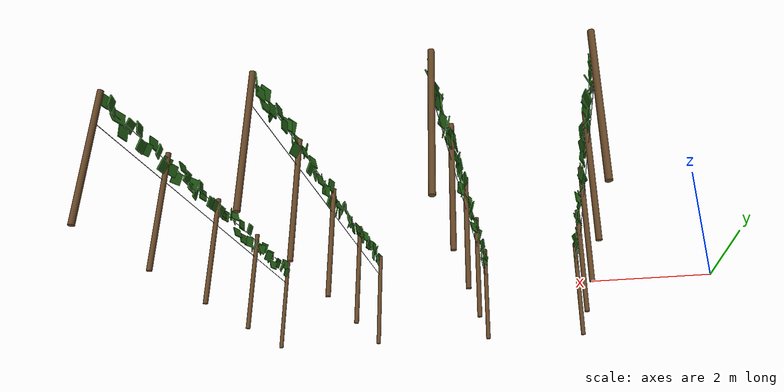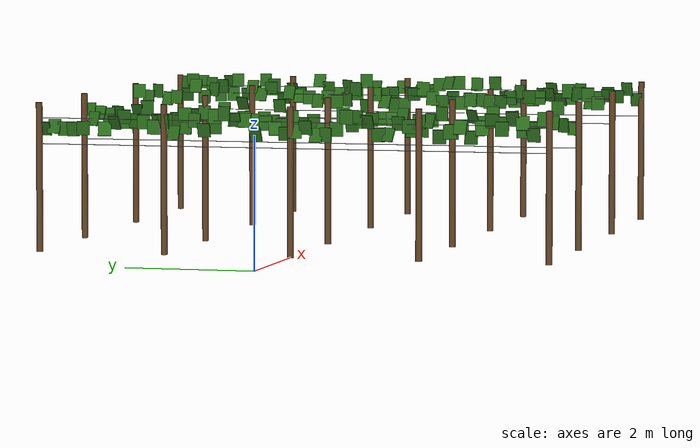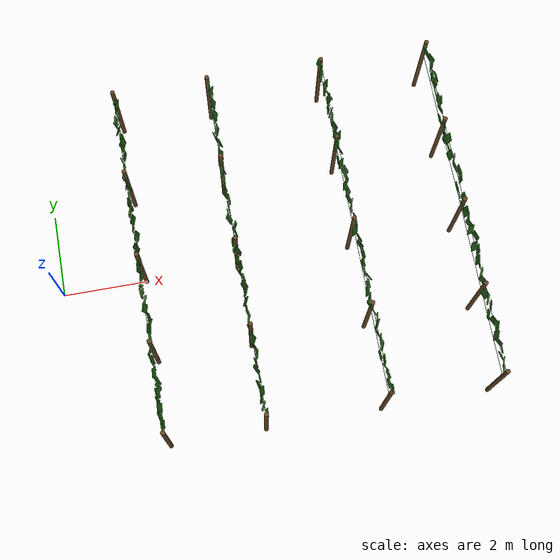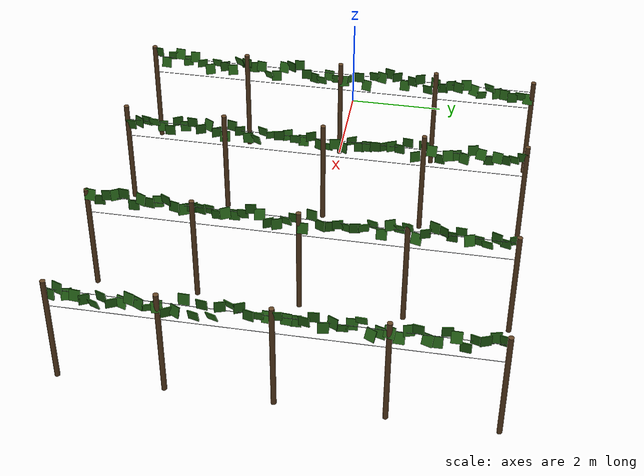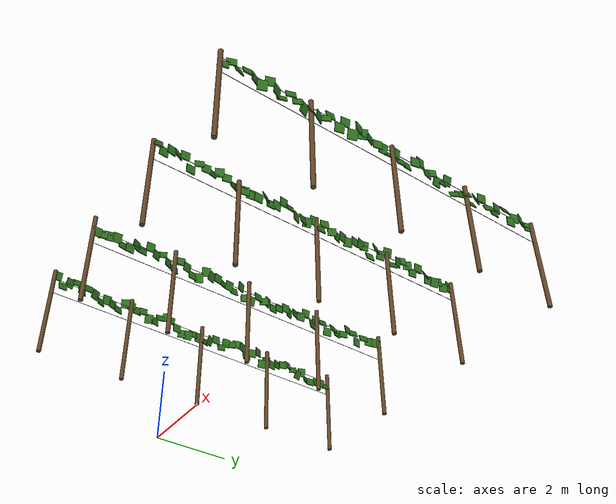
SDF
<?xml version="1.0"?>
<sdf version="1.6">
  <model name="trellis">
    <link name="post_r0_0">
      <pose>2.000 -4.000 1.150 0 0 0</pose>
      <inertial><mass>20</mass>
        <inertia><ixx>5</ixx><ixy>0</ixy><ixz>0</ixz><iyy>5</iyy><iyz>0</iyz><izz>0.2</izz></inertia>
      </inertial>
      <visual name="v">
        <geometry><cylinder><radius>0.05</radius><length>2.30</length></cylinder></geometry>
        <material><ambient>0.20 0.13 0.07 1</ambient><diffuse>0.38 0.26 0.14 1</diffuse></material>
      </visual>
      <collision name="c">
        <geometry><cylinder><radius>0.05</radius><length>2.30</length></cylinder></geometry>
      </collision>
    </link>
    <joint name="fix_post_r0_0" type="fixed">
      <parent>world</parent><child>post_r0_0</child>
    </joint>
    <link name="post_r0_1">
      <pose>2.000 -2.000 1.150 0 0 0</pose>
      <inertial><mass>20</mass>
        <inertia><ixx>5</ixx><ixy>0</ixy><ixz>0</ixz><iyy>5</iyy><iyz>0</iyz><izz>0.2</izz></inertia>
      </inertial>
      <visual name="v">
        <geometry><cylinder><radius>0.05</radius><length>2.30</length></cylinder></geometry>
        <material><ambient>0.20 0.13 0.07 1</ambient><diffuse>0.38 0.26 0.14 1</diffuse></material>
      </visual>
      <collision name="c">
        <geometry><cylinder><radius>0.05</radius><length>2.30</length></cylinder></geometry>
      </collision>
    </link>
    <joint name="fix_post_r0_1" type="fixed">
      <parent>world</parent><child>post_r0_1</child>
    </joint>
    <link name="post_r0_2">
      <pose>2.000 0.000 1.150 0 0 0</pose>
      <inertial><mass>20</mass>
        <inertia><ixx>5</ixx><ixy>0</ixy><ixz>0</ixz><iyy>5</iyy><iyz>0</iyz><izz>0.2</izz></inertia>
      </inertial>
      <visual name="v">
        <geometry><cylinder><radius>0.05</radius><length>2.30</length></cylinder></geometry>
        <material><ambient>0.20 0.13 0.07 1</ambient><diffuse>0.38 0.26 0.14 1</diffuse></material>
      </visual>
      <collision name="c">
        <geometry><cylinder><radius>0.05</radius><length>2.30</length></cylinder></geometry>
      </collision>
    </link>
    <joint name="fix_post_r0_2" type="fixed">
      <parent>world</parent><child>post_r0_2</child>
    </joint>
    <link name="post_r0_3">
      <pose>2.000 2.000 1.150 0 0 0</pose>
      <inertial><mass>20</mass>
        <inertia><ixx>5</ixx><ixy>0</ixy><ixz>0</ixz><iyy>5</iyy><iyz>0</iyz><izz>0.2</izz></inertia>
      </inertial>
      <visual name="v">
        <geometry><cylinder><radius>0.05</radius><length>2.30</length></cylinder></geometry>
        <material><ambient>0.20 0.13 0.07 1</ambient><diffuse>0.38 0.26 0.14 1</diffuse></material>
      </visual>
      <collision name="c">
        <geometry><cylinder><radius>0.05</radius><length>2.30</length></cylinder></geometry>
      </collision>
    </link>
    <joint name="fix_post_r0_3" type="fixed">
      <parent>world</parent><child>post_r0_3</child>
    </joint>
    <link name="post_r0_4">
      <pose>2.000 4.000 1.150 0 0 0</pose>
      <inertial><mass>20</mass>
        <inertia><ixx>5</ixx><ixy>0</ixy><ixz>0</ixz><iyy>5</iyy><iyz>0</iyz><izz>0.2</izz></inertia>
      </inertial>
      <visual name="v">
        <geometry><cylinder><radius>0.05</radius><length>2.30</length></cylinder></geometry>
        <material><ambient>0.20 0.13 0.07 1</ambient><diffuse>0.38 0.26 0.14 1</diffuse></material>
      </visual>
      <collision name="c">
        <geometry><cylinder><radius>0.05</radius><length>2.30</length></cylinder></geometry>
      </collision>
    </link>
    <joint name="fix_post_r0_4" type="fixed">
      <parent>world</parent><child>post_r0_4</child>
    </joint>
    <link name="wire_r0_fruit">
      <pose>2.000 0 1.665 1.5708 0 0</pose>
      <inertial><mass>1.0</mass>
        <inertia><ixx>0.2</ixx><ixy>0</ixy><ixz>0</ixz><iyy>0.2</iyy><iyz>0</iyz><izz>0.001</izz></inertia>
      </inertial>
      <visual name="v">
        <geometry><cylinder><radius>0.004</radius><length>8.00</length></cylinder></geometry>
        <material><ambient>0.30 0.30 0.32 1</ambient><diffuse>0.55 0.56 0.58 1</diffuse></material>
      </visual>
      <collision name="c">
        <geometry><cylinder><radius>0.004</radius><length>8.00</length></cylinder></geometry>
      </collision>
    </link>
    <joint name="fix_wire_r0_fruit" type="fixed">
      <parent>world</parent><child>wire_r0_fruit</child>
    </joint>
    <link name="wire_r0_canopy">
      <pose>2.000 0 2.065 1.5708 0 0</pose>
      <inertial><mass>1.0</mass>
        <inertia><ixx>0.2</ixx><ixy>0</ixy><ixz>0</ixz><iyy>0.2</iyy><iyz>0</iyz><izz>0.001</izz></inertia>
      </inertial>
      <visual name="v">
        <geometry><cylinder><radius>0.004</radius><length>8.00</length></cylinder></geometry>
        <material><ambient>0.30 0.30 0.32 1</ambient><diffuse>0.55 0.56 0.58 1</diffuse></material>
      </visual>
      <collision name="c">
        <geometry><cylinder><radius>0.004</radius><length>8.00</length></cylinder></geometry>
      </collision>
    </link>
    <joint name="fix_wire_r0_canopy" type="fixed">
      <parent>world</parent><child>wire_r0_canopy</child>
    </joint>
    <link name="post_r1_0">
      <pose>4.226 -4.000 1.150 0 0 0</pose>
      <inertial><mass>20</mass>
        <inertia><ixx>5</ixx><ixy>0</ixy><ixz>0</ixz><iyy>5</iyy><iyz>0</iyz><izz>0.2</izz></inertia>
      </inertial>
      <visual name="v">
        <geometry><cylinder><radius>0.05</radius><length>2.30</length></cylinder></geometry>
        <material><ambient>0.20 0.13 0.07 1</ambient><diffuse>0.38 0.26 0.14 1</diffuse></material>
      </visual>
      <collision name="c">
        <geometry><cylinder><radius>0.05</radius><length>2.30</length></cylinder></geometry>
      </collision>
    </link>
    <joint name="fix_post_r1_0" type="fixed">
      <parent>world</parent><child>post_r1_0</child>
    </joint>
    <link name="post_r1_1">
      <pose>4.226 -2.000 1.150 0 0 0</pose>
      <inertial><mass>20</mass>
        <inertia><ixx>5</ixx><ixy>0</ixy><ixz>0</ixz><iyy>5</iyy><iyz>0</iyz><izz>0.2</izz></inertia>
      </inertial>
      <visual name="v">
        <geometry><cylinder><radius>0.05</radius><length>2.30</length></cylinder></geometry>
        <material><ambient>0.20 0.13 0.07 1</ambient><diffuse>0.38 0.26 0.14 1</diffuse></material>
      </visual>
      <collision name="c">
        <geometry><cylinder><radius>0.05</radius><length>2.30</length></cylinder></geometry>
      </collision>
    </link>
    <joint name="fix_post_r1_1" type="fixed">
      <parent>world</parent><child>post_r1_1</child>
    </joint>
    <link name="post_r1_2">
      <pose>4.226 0.000 1.150 0 0 0</pose>
      <inertial><mass>20</mass>
        <inertia><ixx>5</ixx><ixy>0</ixy><ixz>0</ixz><iyy>5</iyy><iyz>0</iyz><izz>0.2</izz></inertia>
      </inertial>
      <visual name="v">
        <geometry><cylinder><radius>0.05</radius><length>2.30</length></cylinder></geometry>
        <material><ambient>0.20 0.13 0.07 1</ambient><diffuse>0.38 0.26 0.14 1</diffuse></material>
      </visual>
      <collision name="c">
        <geometry><cylinder><radius>0.05</radius><length>2.30</length></cylinder></geometry>
      </collision>
    </link>
    <joint name="fix_post_r1_2" type="fixed">
      <parent>world</parent><child>post_r1_2</child>
    </joint>
    <link name="post_r1_3">
      <pose>4.226 2.000 1.150 0 0 0</pose>
      <inertial><mass>20</mass>
        <inertia><ixx>5</ixx><ixy>0</ixy><ixz>0</ixz><iyy>5</iyy><iyz>0</iyz><izz>0.2</izz></inertia>
      </inertial>
      <visual name="v">
        <geometry><cylinder><radius>0.05</radius><length>2.30</length></cylinder></geometry>
        <material><ambient>0.20 0.13 0.07 1</ambient><diffuse>0.38 0.26 0.14 1</diffuse></material>
      </visual>
      <collision name="c">
        <geometry><cylinder><radius>0.05</radius><length>2.30</length></cylinder></geometry>
      </collision>
    </link>
    <joint name="fix_post_r1_3" type="fixed">
      <parent>world</parent><child>post_r1_3</child>
    </joint>
    <link name="post_r1_4">
      <pose>4.226 4.000 1.150 0 0 0</pose>
      <inertial><mass>20</mass>
        <inertia><ixx>5</ixx><ixy>0</ixy><ixz>0</ixz><iyy>5</iyy><iyz>0</iyz><izz>0.2</izz></inertia>
      </inertial>
      <visual name="v">
        <geometry><cylinder><radius>0.05</radius><length>2.30</length></cylinder></geometry>
        <material><ambient>0.20 0.13 0.07 1</ambient><diffuse>0.38 0.26 0.14 1</diffuse></material>
      </visual>
      <collision name="c">
        <geometry><cylinder><radius>0.05</radius><length>2.30</length></cylinder></geometry>
      </collision>
    </link>
    <joint name="fix_post_r1_4" type="fixed">
      <parent>world</parent><child>post_r1_4</child>
    </joint>
    <link name="wire_r1_fruit">
      <pose>4.226 0 1.582 1.5708 0 0</pose>
      <inertial><mass>1.0</mass>
        <inertia><ixx>0.2</ixx><ixy>0</ixy><ixz>0</ixz><iyy>0.2</iyy><iyz>0</iyz><izz>0.001</izz></inertia>
      </inertial>
      <visual name="v">
        <geometry><cylinder><radius>0.004</radius><length>8.00</length></cylinder></geometry>
        <material><ambient>0.30 0.30 0.32 1</ambient><diffuse>0.55 0.56 0.58 1</diffuse></material>
      </visual>
      <collision name="c">
        <geometry><cylinder><radius>0.004</radius><length>8.00</length></cylinder></geometry>
      </collision>
    </link>
    <joint name="fix_wire_r1_fruit" type="fixed">
      <parent>world</parent><child>wire_r1_fruit</child>
    </joint>
    <link name="wire_r1_canopy">
      <pose>4.226 0 1.982 1.5708 0 0</pose>
      <inertial><mass>1.0</mass>
        <inertia><ixx>0.2</ixx><ixy>0</ixy><ixz>0</ixz><iyy>0.2</iyy><iyz>0</iyz><izz>0.001</izz></inertia>
      </inertial>
      <visual name="v">
        <geometry><cylinder><radius>0.004</radius><length>8.00</length></cylinder></geometry>
        <material><ambient>0.30 0.30 0.32 1</ambient><diffuse>0.55 0.56 0.58 1</diffuse></material>
      </visual>
      <collision name="c">
        <geometry><cylinder><radius>0.004</radius><length>8.00</length></cylinder></geometry>
      </collision>
    </link>
    <joint name="fix_wire_r1_canopy" type="fixed">
      <parent>world</parent><child>wire_r1_canopy</child>
    </joint>
    <link name="post_r2_0">
      <pose>6.945 -4.000 1.150 0 0 0</pose>
      <inertial><mass>20</mass>
        <inertia><ixx>5</ixx><ixy>0</ixy><ixz>0</ixz><iyy>5</iyy><iyz>0</iyz><izz>0.2</izz></inertia>
      </inertial>
      <visual name="v">
        <geometry><cylinder><radius>0.05</radius><length>2.30</length></cylinder></geometry>
        <material><ambient>0.20 0.13 0.07 1</ambient><diffuse>0.38 0.26 0.14 1</diffuse></material>
      </visual>
      <collision name="c">
        <geometry><cylinder><radius>0.05</radius><length>2.30</length></cylinder></geometry>
      </collision>
    </link>
    <joint name="fix_post_r2_0" type="fixed">
      <parent>world</parent><child>post_r2_0</child>
    </joint>
    <link name="post_r2_1">
      <pose>6.945 -2.000 1.150 0 0 0</pose>
      <inertial><mass>20</mass>
        <inertia><ixx>5</ixx><ixy>0</ixy><ixz>0</ixz><iyy>5</iyy><iyz>0</iyz><izz>0.2</izz></inertia>
      </inertial>
      <visual name="v">
        <geometry><cylinder><radius>0.05</radius><length>2.30</length></cylinder></geometry>
        <material><ambient>0.20 0.13 0.07 1</ambient><diffuse>0.38 0.26 0.14 1</diffuse></material>
      </visual>
      <collision name="c">
        <geometry><cylinder><radius>0.05</radius><length>2.30</length></cylinder></geometry>
      </collision>
    </link>
    <joint name="fix_post_r2_1" type="fixed">
      <parent>world</parent><child>post_r2_1</child>
    </joint>
    <link name="post_r2_2">
      <pose>6.945 0.000 1.150 0 0 0</pose>
      <inertial><mass>20</mass>
        <inertia><ixx>5</ixx><ixy>0</ixy><ixz>0</ixz><iyy>5</iyy><iyz>0</iyz><izz>0.2</izz></inertia>
      </inertial>
      <visual name="v">
        <geometry><cylinder><radius>0.05</radius><length>2.30</length></cylinder></geometry>
        <material><ambient>0.20 0.13 0.07 1</ambient><diffuse>0.38 0.26 0.14 1</diffuse></material>
      </visual>
      <collision name="c">
        <geometry><cylinder><radius>0.05</radius><length>2.30</length></cylinder></geometry>
      </collision>
    </link>
    <joint name="fix_post_r2_2" type="fixed">
      <parent>world</parent><child>post_r2_2</child>
    </joint>
    <link name="post_r2_3">
      <pose>6.945 2.000 1.150 0 0 0</pose>
      <inertial><mass>20</mass>
        <inertia><ixx>5</ixx><ixy>0</ixy><ixz>0</ixz><iyy>5</iyy><iyz>0</iyz><izz>0.2</izz></inertia>
      </inertial>
      <visual name="v">
        <geometry><cylinder><radius>0.05</radius><length>2.30</length></cylinder></geometry>
        <material><ambient>0.20 0.13 0.07 1</ambient><diffuse>0.38 0.26 0.14 1</diffuse></material>
      </visual>
      <collision name="c">
        <geometry><cylinder><radius>0.05</radius><length>2.30</length></cylinder></geometry>
      </collision>
    </link>
    <joint name="fix_post_r2_3" type="fixed">
      <parent>world</parent><child>post_r2_3</child>
    </joint>
    <link name="post_r2_4">
      <pose>6.945 4.000 1.150 0 0 0</pose>
      <inertial><mass>20</mass>
        <inertia><ixx>5</ixx><ixy>0</ixy><ixz>0</ixz><iyy>5</iyy><iyz>0</iyz><izz>0.2</izz></inertia>
      </inertial>
      <visual name="v">
        <geometry><cylinder><radius>0.05</radius><length>2.30</length></cylinder></geometry>
        <material><ambient>0.20 0.13 0.07 1</ambient><diffuse>0.38 0.26 0.14 1</diffuse></material>
      </visual>
      <collision name="c">
        <geometry><cylinder><radius>0.05</radius><length>2.30</length></cylinder></geometry>
      </collision>
    </link>
    <joint name="fix_post_r2_4" type="fixed">
      <parent>world</parent><child>post_r2_4</child>
    </joint>
    <link name="wire_r2_fruit">
      <pose>6.945 0 1.773 1.5708 0 0</pose>
      <inertial><mass>1.0</mass>
        <inertia><ixx>0.2</ixx><ixy>0</ixy><ixz>0</ixz><iyy>0.2</iyy><iyz>0</iyz><izz>0.001</izz></inertia>
      </inertial>
      <visual name="v">
        <geometry><cylinder><radius>0.004</radius><length>8.00</length></cylinder></geometry>
        <material><ambient>0.30 0.30 0.32 1</ambient><diffuse>0.55 0.56 0.58 1</diffuse></material>
      </visual>
      <collision name="c">
        <geometry><cylinder><radius>0.004</radius><length>8.00</length></cylinder></geometry>
      </collision>
    </link>
    <joint name="fix_wire_r2_fruit" type="fixed">
      <parent>world</parent><child>wire_r2_fruit</child>
    </joint>
    <link name="wire_r2_canopy">
      <pose>6.945 0 2.173 1.5708 0 0</pose>
      <inertial><mass>1.0</mass>
        <inertia><ixx>0.2</ixx><ixy>0</ixy><ixz>0</ixz><iyy>0.2</iyy><iyz>0</iyz><izz>0.001</izz></inertia>
      </inertial>
      <visual name="v">
        <geometry><cylinder><radius>0.004</radius><length>8.00</length></cylinder></geometry>
        <material><ambient>0.30 0.30 0.32 1</ambient><diffuse>0.55 0.56 0.58 1</diffuse></material>
      </visual>
      <collision name="c">
        <geometry><cylinder><radius>0.004</radius><length>8.00</length></cylinder></geometry>
      </collision>
    </link>
    <joint name="fix_wire_r2_canopy" type="fixed">
      <parent>world</parent><child>wire_r2_canopy</child>
    </joint>
    <link name="post_r3_0">
      <pose>9.493 -4.000 1.150 0 0 0</pose>
      <inertial><mass>20</mass>
        <inertia><ixx>5</ixx><ixy>0</ixy><ixz>0</ixz><iyy>5</iyy><iyz>0</iyz><izz>0.2</izz></inertia>
      </inertial>
      <visual name="v">
        <geometry><cylinder><radius>0.05</radius><length>2.30</length></cylinder></geometry>
        <material><ambient>0.20 0.13 0.07 1</ambient><diffuse>0.38 0.26 0.14 1</diffuse></material>
      </visual>
      <collision name="c">
        <geometry><cylinder><radius>0.05</radius><length>2.30</length></cylinder></geometry>
      </collision>
    </link>
    <joint name="fix_post_r3_0" type="fixed">
      <parent>world</parent><child>post_r3_0</child>
    </joint>
    <link name="post_r3_1">
      <pose>9.493 -2.000 1.150 0 0 0</pose>
      <inertial><mass>20</mass>
        <inertia><ixx>5</ixx><ixy>0</ixy><ixz>0</ixz><iyy>5</iyy><iyz>0</iyz><izz>0.2</izz></inertia>
      </inertial>
      <visual name="v">
        <geometry><cylinder><radius>0.05</radius><length>2.30</length></cylinder></geometry>
        <material><ambient>0.20 0.13 0.07 1</ambient><diffuse>0.38 0.26 0.14 1</diffuse></material>
      </visual>
      <collision name="c">
        <geometry><cylinder><radius>0.05</radius><length>2.30</length></cylinder></geometry>
      </collision>
    </link>
    <joint name="fix_post_r3_1" type="fixed">
      <parent>world</parent><child>post_r3_1</child>
    </joint>
    <link name="post_r3_2">
      <pose>9.493 0.000 1.150 0 0 0</pose>
      <inertial><mass>20</mass>
        <inertia><ixx>5</ixx><ixy>0</ixy><ixz>0</ixz><iyy>5</iyy><iyz>0</iyz><izz>0.2</izz></inertia>
      </inertial>
      <visual name="v">
        <geometry><cylinder><radius>0.05</radius><length>2.30</length></cylinder></geometry>
        <material><ambient>0.20 0.13 0.07 1</ambient><diffuse>0.38 0.26 0.14 1</diffuse></material>
      </visual>
      <collision name="c">
        <geometry><cylinder><radius>0.05</radius><length>2.30</length></cylinder></geometry>
      </collision>
    </link>
    <joint name="fix_post_r3_2" type="fixed">
      <parent>world</parent><child>post_r3_2</child>
    </joint>
    <link name="post_r3_3">
      <pose>9.493 2.000 1.150 0 0 0</pose>
      <inertial><mass>20</mass>
        <inertia><ixx>5</ixx><ixy>0</ixy><ixz>0</ixz><iyy>5</iyy><iyz>0</iyz><izz>0.2</izz></inertia>
      </inertial>
      <visual name="v">
        <geometry><cylinder><radius>0.05</radius><length>2.30</length></cylinder></geometry>
        <material><ambient>0.20 0.13 0.07 1</ambient><diffuse>0.38 0.26 0.14 1</diffuse></material>
      </visual>
      <collision name="c">
        <geometry><cylinder><radius>0.05</radius><length>2.30</length></cylinder></geometry>
      </collision>
    </link>
    <joint name="fix_post_r3_3" type="fixed">
      <parent>world</parent><child>post_r3_3</child>
    </joint>
    <link name="post_r3_4">
      <pose>9.493 4.000 1.150 0 0 0</pose>
      <inertial><mass>20</mass>
        <inertia><ixx>5</ixx><ixy>0</ixy><ixz>0</ixz><iyy>5</iyy><iyz>0</iyz><izz>0.2</izz></inertia>
      </inertial>
      <visual name="v">
        <geometry><cylinder><radius>0.05</radius><length>2.30</length></cylinder></geometry>
        <material><ambient>0.20 0.13 0.07 1</ambient><diffuse>0.38 0.26 0.14 1</diffuse></material>
      </visual>
      <collision name="c">
        <geometry><cylinder><radius>0.05</radius><length>2.30</length></cylinder></geometry>
      </collision>
    </link>
    <joint name="fix_post_r3_4" type="fixed">
      <parent>world</parent><child>post_r3_4</child>
    </joint>
    <link name="wire_r3_fruit">
      <pose>9.493 0 1.726 1.5708 0 0</pose>
      <inertial><mass>1.0</mass>
        <inertia><ixx>0.2</ixx><ixy>0</ixy><ixz>0</ixz><iyy>0.2</iyy><iyz>0</iyz><izz>0.001</izz></inertia>
      </inertial>
      <visual name="v">
        <geometry><cylinder><radius>0.004</radius><length>8.00</length></cylinder></geometry>
        <material><ambient>0.30 0.30 0.32 1</ambient><diffuse>0.55 0.56 0.58 1</diffuse></material>
      </visual>
      <collision name="c">
        <geometry><cylinder><radius>0.004</radius><length>8.00</length></cylinder></geometry>
      </collision>
    </link>
    <joint name="fix_wire_r3_fruit" type="fixed">
      <parent>world</parent><child>wire_r3_fruit</child>
    </joint>
    <link name="wire_r3_canopy">
      <pose>9.493 0 2.126 1.5708 0 0</pose>
      <inertial><mass>1.0</mass>
        <inertia><ixx>0.2</ixx><ixy>0</ixy><ixz>0</ixz><iyy>0.2</iyy><iyz>0</iyz><izz>0.001</izz></inertia>
      </inertial>
      <visual name="v">
        <geometry><cylinder><radius>0.004</radius><length>8.00</length></cylinder></geometry>
        <material><ambient>0.30 0.30 0.32 1</ambient><diffuse>0.55 0.56 0.58 1</diffuse></material>
      </visual>
      <collision name="c">
        <geometry><cylinder><radius>0.004</radius><length>8.00</length></cylinder></geometry>
      </collision>
    </link>
    <joint name="fix_wire_r3_canopy" type="fixed">
      <parent>world</parent><child>wire_r3_canopy</child>
    </joint>
    <link name="canopy">
      <pose>0 0 0 0 0 0</pose>
      <inertial><mass>2.0</mass>
        <inertia><ixx>1</ixx><ixy>0</ixy><ixz>0</ixz><iyy>1</iyy><iyz>0</iyz><izz>1</izz></inertia>
      </inertial>
      <visual name="leaf_r0_0">
        <pose>1.998 -3.920 2.174 0 0.18 -0.03</pose>
        <geometry><box><size>0.02 0.20 0.22</size></box></geometry>
        <material><ambient>0.08 0.20 0.05 1</ambient><diffuse>0.16 0.42 0.10 1</diffuse></material>
      </visual>
      <visual name="leaf_r0_1">
        <pose>2.002 -3.760 1.936 0 -0.27 -0.05</pose>
        <geometry><box><size>0.02 0.20 0.22</size></box></geometry>
        <material><ambient>0.08 0.20 0.05 1</ambient><diffuse>0.16 0.42 0.10 1</diffuse></material>
      </visual>
      <visual name="leaf_r0_2">
        <pose>1.986 -3.600 2.111 0 0.32 0.22</pose>
        <geometry><box><size>0.02 0.20 0.22</size></box></geometry>
        <material><ambient>0.08 0.20 0.05 1</ambient><diffuse>0.16 0.42 0.10 1</diffuse></material>
      </visual>
      <visual name="leaf_r0_3">
        <pose>2.008 -3.440 2.178 0 -0.38 -0.07</pose>
        <geometry><box><size>0.02 0.20 0.22</size></box></geometry>
        <material><ambient>0.08 0.20 0.05 1</ambient><diffuse>0.16 0.42 0.10 1</diffuse></material>
      </visual>
      <visual name="leaf_r0_4">
        <pose>1.986 -3.280 2.018 0 -0.16 0.25</pose>
        <geometry><box><size>0.02 0.20 0.22</size></box></geometry>
        <material><ambient>0.08 0.20 0.05 1</ambient><diffuse>0.16 0.42 0.10 1</diffuse></material>
      </visual>
      <visual name="leaf_r0_5">
        <pose>2.007 -3.120 2.137 0 -0.30 0.05</pose>
        <geometry><box><size>0.02 0.20 0.22</size></box></geometry>
        <material><ambient>0.08 0.20 0.05 1</ambient><diffuse>0.16 0.42 0.10 1</diffuse></material>
      </visual>
      <visual name="leaf_r0_6">
        <pose>2.036 -2.960 2.017 0 0.32 0.41</pose>
        <geometry><box><size>0.02 0.20 0.22</size></box></geometry>
        <material><ambient>0.08 0.20 0.05 1</ambient><diffuse>0.16 0.42 0.10 1</diffuse></material>
      </visual>
      <visual name="leaf_r0_7">
        <pose>2.026 -2.800 1.880 0 -0.28 0.41</pose>
        <geometry><box><size>0.02 0.20 0.22</size></box></geometry>
        <material><ambient>0.08 0.20 0.05 1</ambient><diffuse>0.16 0.42 0.10 1</diffuse></material>
      </visual>
      <visual name="leaf_r0_8">
        <pose>1.985 -2.640 2.031 0 0.38 -0.09</pose>
        <geometry><box><size>0.02 0.20 0.22</size></box></geometry>
        <material><ambient>0.08 0.20 0.05 1</ambient><diffuse>0.16 0.42 0.10 1</diffuse></material>
      </visual>
      <visual name="leaf_r0_9">
        <pose>1.993 -2.480 1.965 0 -0.01 0.37</pose>
        <geometry><box><size>0.02 0.20 0.22</size></box></geometry>
        <material><ambient>0.08 0.20 0.05 1</ambient><diffuse>0.16 0.42 0.10 1</diffuse></material>
      </visual>
      <visual name="leaf_r0_10">
        <pose>1.976 -2.320 1.885 0 -0.27 0.23</pose>
        <geometry><box><size>0.02 0.20 0.22</size></box></geometry>
        <material><ambient>0.08 0.20 0.05 1</ambient><diffuse>0.16 0.42 0.10 1</diffuse></material>
      </visual>
      <visual name="leaf_r0_11">
        <pose>1.993 -2.160 2.119 0 0.34 -0.48</pose>
        <geometry><box><size>0.02 0.20 0.22</size></box></geometry>
        <material><ambient>0.08 0.20 0.05 1</ambient><diffuse>0.16 0.42 0.10 1</diffuse></material>
      </visual>
      <visual name="leaf_r0_12">
        <pose>2.012 -2.000 2.104 0 0.01 -0.10</pose>
        <geometry><box><size>0.02 0.20 0.22</size></box></geometry>
        <material><ambient>0.08 0.20 0.05 1</ambient><diffuse>0.16 0.42 0.10 1</diffuse></material>
      </visual>
      <visual name="leaf_r0_13">
        <pose>2.012 -1.840 2.031 0 -0.12 0.08</pose>
        <geometry><box><size>0.02 0.20 0.22</size></box></geometry>
        <material><ambient>0.08 0.20 0.05 1</ambient><diffuse>0.16 0.42 0.10 1</diffuse></material>
      </visual>
      <visual name="leaf_r0_14">
        <pose>2.020 -1.680 2.071 0 -0.22 -0.14</pose>
        <geometry><box><size>0.02 0.20 0.22</size></box></geometry>
        <material><ambient>0.08 0.20 0.05 1</ambient><diffuse>0.16 0.42 0.10 1</diffuse></material>
      </visual>
      <visual name="leaf_r0_15">
        <pose>2.041 -1.520 1.899 0 0.40 -0.41</pose>
        <geometry><box><size>0.02 0.20 0.22</size></box></geometry>
        <material><ambient>0.08 0.20 0.05 1</ambient><diffuse>0.16 0.42 0.10 1</diffuse></material>
      </visual>
      <visual name="leaf_r0_16">
        <pose>2.048 -1.360 1.891 0 -0.18 0.22</pose>
        <geometry><box><size>0.02 0.20 0.22</size></box></geometry>
        <material><ambient>0.08 0.20 0.05 1</ambient><diffuse>0.16 0.42 0.10 1</diffuse></material>
      </visual>
      <visual name="leaf_r0_17">
        <pose>1.998 -1.200 2.089 0 -0.35 -0.23</pose>
        <geometry><box><size>0.02 0.20 0.22</size></box></geometry>
        <material><ambient>0.08 0.20 0.05 1</ambient><diffuse>0.16 0.42 0.10 1</diffuse></material>
      </visual>
      <visual name="leaf_r0_18">
        <pose>2.030 -1.040 2.149 0 0.08 -0.46</pose>
        <geometry><box><size>0.02 0.20 0.22</size></box></geometry>
        <material><ambient>0.08 0.20 0.05 1</ambient><diffuse>0.16 0.42 0.10 1</diffuse></material>
      </visual>
      <visual name="leaf_r0_19">
        <pose>1.970 -0.880 2.158 0 -0.10 0.07</pose>
        <geometry><box><size>0.02 0.20 0.22</size></box></geometry>
        <material><ambient>0.08 0.20 0.05 1</ambient><diffuse>0.16 0.42 0.10 1</diffuse></material>
      </visual>
      <visual name="leaf_r0_20">
        <pose>1.998 -0.720 1.970 0 -0.00 0.06</pose>
        <geometry><box><size>0.02 0.20 0.22</size></box></geometry>
        <material><ambient>0.08 0.20 0.05 1</ambient><diffuse>0.16 0.42 0.10 1</diffuse></material>
      </visual>
      <visual name="leaf_r0_21">
        <pose>1.972 -0.560 1.882 0 -0.00 -0.31</pose>
        <geometry><box><size>0.02 0.20 0.22</size></box></geometry>
        <material><ambient>0.08 0.20 0.05 1</ambient><diffuse>0.16 0.42 0.10 1</diffuse></material>
      </visual>
      <visual name="leaf_r0_22">
        <pose>2.015 -0.400 1.869 0 0.37 -0.15</pose>
        <geometry><box><size>0.02 0.20 0.22</size></box></geometry>
        <material><ambient>0.08 0.20 0.05 1</ambient><diffuse>0.16 0.42 0.10 1</diffuse></material>
      </visual>
      <visual name="leaf_r0_23">
        <pose>1.985 -0.240 1.986 0 -0.25 -0.11</pose>
        <geometry><box><size>0.02 0.20 0.22</size></box></geometry>
        <material><ambient>0.08 0.20 0.05 1</ambient><diffuse>0.16 0.42 0.10 1</diffuse></material>
      </visual>
      <visual name="leaf_r0_24">
        <pose>1.995 -0.080 1.925 0 0.28 0.08</pose>
        <geometry><box><size>0.02 0.20 0.22</size></box></geometry>
        <material><ambient>0.08 0.20 0.05 1</ambient><diffuse>0.16 0.42 0.10 1</diffuse></material>
      </visual>
      <visual name="leaf_r0_25">
        <pose>2.001 0.080 1.888 0 -0.30 0.23</pose>
        <geometry><box><size>0.02 0.20 0.22</size></box></geometry>
        <material><ambient>0.08 0.20 0.05 1</ambient><diffuse>0.16 0.42 0.10 1</diffuse></material>
      </visual>
      <visual name="leaf_r0_26">
        <pose>2.002 0.240 1.967 0 0.35 0.46</pose>
        <geometry><box><size>0.02 0.20 0.22</size></box></geometry>
        <material><ambient>0.08 0.20 0.05 1</ambient><diffuse>0.16 0.42 0.10 1</diffuse></material>
      </visual>
      <visual name="leaf_r0_27">
        <pose>2.033 0.400 2.040 0 0.01 -0.01</pose>
        <geometry><box><size>0.02 0.20 0.22</size></box></geometry>
        <material><ambient>0.08 0.20 0.05 1</ambient><diffuse>0.16 0.42 0.10 1</diffuse></material>
      </visual>
      <visual name="leaf_r0_28">
        <pose>2.045 0.560 1.865 0 -0.30 -0.26</pose>
        <geometry><box><size>0.02 0.20 0.22</size></box></geometry>
        <material><ambient>0.08 0.20 0.05 1</ambient><diffuse>0.16 0.42 0.10 1</diffuse></material>
      </visual>
      <visual name="leaf_r0_29">
        <pose>2.005 0.720 2.080 0 0.20 -0.09</pose>
        <geometry><box><size>0.02 0.20 0.22</size></box></geometry>
        <material><ambient>0.08 0.20 0.05 1</ambient><diffuse>0.16 0.42 0.10 1</diffuse></material>
      </visual>
      <visual name="leaf_r0_30">
        <pose>2.023 0.880 2.084 0 -0.24 -0.31</pose>
        <geometry><box><size>0.02 0.20 0.22</size></box></geometry>
        <material><ambient>0.08 0.20 0.05 1</ambient><diffuse>0.16 0.42 0.10 1</diffuse></material>
      </visual>
      <visual name="leaf_r0_31">
        <pose>1.991 1.040 2.175 0 -0.01 -0.29</pose>
        <geometry><box><size>0.02 0.20 0.22</size></box></geometry>
        <material><ambient>0.08 0.20 0.05 1</ambient><diffuse>0.16 0.42 0.10 1</diffuse></material>
      </visual>
      <visual name="leaf_r0_32">
        <pose>2.024 1.200 2.131 0 0.12 0.41</pose>
        <geometry><box><size>0.02 0.20 0.22</size></box></geometry>
        <material><ambient>0.08 0.20 0.05 1</ambient><diffuse>0.16 0.42 0.10 1</diffuse></material>
      </visual>
      <visual name="leaf_r0_33">
        <pose>1.990 1.360 1.920 0 -0.25 -0.08</pose>
        <geometry><box><size>0.02 0.20 0.22</size></box></geometry>
        <material><ambient>0.08 0.20 0.05 1</ambient><diffuse>0.16 0.42 0.10 1</diffuse></material>
      </visual>
      <visual name="leaf_r0_34">
        <pose>2.022 1.520 2.061 0 0.10 -0.23</pose>
        <geometry><box><size>0.02 0.20 0.22</size></box></geometry>
        <material><ambient>0.08 0.20 0.05 1</ambient><diffuse>0.16 0.42 0.10 1</diffuse></material>
      </visual>
      <visual name="leaf_r0_35">
        <pose>2.046 1.680 2.145 0 0.01 0.36</pose>
        <geometry><box><size>0.02 0.20 0.22</size></box></geometry>
        <material><ambient>0.08 0.20 0.05 1</ambient><diffuse>0.16 0.42 0.10 1</diffuse></material>
      </visual>
      <visual name="leaf_r0_36">
        <pose>1.988 1.840 1.872 0 0.23 -0.24</pose>
        <geometry><box><size>0.02 0.20 0.22</size></box></geometry>
        <material><ambient>0.08 0.20 0.05 1</ambient><diffuse>0.16 0.42 0.10 1</diffuse></material>
      </visual>
      <visual name="leaf_r0_37">
        <pose>1.979 2.000 2.040 0 -0.11 -0.39</pose>
        <geometry><box><size>0.02 0.20 0.22</size></box></geometry>
        <material><ambient>0.08 0.20 0.05 1</ambient><diffuse>0.16 0.42 0.10 1</diffuse></material>
      </visual>
      <visual name="leaf_r0_38">
        <pose>1.997 2.160 1.950 0 0.06 0.12</pose>
        <geometry><box><size>0.02 0.20 0.22</size></box></geometry>
        <material><ambient>0.08 0.20 0.05 1</ambient><diffuse>0.16 0.42 0.10 1</diffuse></material>
      </visual>
      <visual name="leaf_r0_39">
        <pose>1.992 2.320 2.026 0 -0.05 0.31</pose>
        <geometry><box><size>0.02 0.20 0.22</size></box></geometry>
        <material><ambient>0.08 0.20 0.05 1</ambient><diffuse>0.16 0.42 0.10 1</diffuse></material>
      </visual>
      <visual name="leaf_r0_40">
        <pose>2.049 2.480 2.040 0 -0.11 -0.30</pose>
        <geometry><box><size>0.02 0.20 0.22</size></box></geometry>
        <material><ambient>0.08 0.20 0.05 1</ambient><diffuse>0.16 0.42 0.10 1</diffuse></material>
      </visual>
      <visual name="leaf_r0_41">
        <pose>2.033 2.640 2.103 0 -0.26 0.21</pose>
        <geometry><box><size>0.02 0.20 0.22</size></box></geometry>
        <material><ambient>0.08 0.20 0.05 1</ambient><diffuse>0.16 0.42 0.10 1</diffuse></material>
      </visual>
      <visual name="leaf_r0_42">
        <pose>2.043 2.800 2.006 0 -0.37 -0.40</pose>
        <geometry><box><size>0.02 0.20 0.22</size></box></geometry>
        <material><ambient>0.08 0.20 0.05 1</ambient><diffuse>0.16 0.42 0.10 1</diffuse></material>
      </visual>
      <visual name="leaf_r0_43">
        <pose>2.041 2.960 1.906 0 0.36 0.22</pose>
        <geometry><box><size>0.02 0.20 0.22</size></box></geometry>
        <material><ambient>0.08 0.20 0.05 1</ambient><diffuse>0.16 0.42 0.10 1</diffuse></material>
      </visual>
      <visual name="leaf_r0_44">
        <pose>1.997 3.120 2.064 0 0.36 -0.38</pose>
        <geometry><box><size>0.02 0.20 0.22</size></box></geometry>
        <material><ambient>0.08 0.20 0.05 1</ambient><diffuse>0.16 0.42 0.10 1</diffuse></material>
      </visual>
      <visual name="leaf_r0_45">
        <pose>1.959 3.280 1.918 0 -0.19 0.43</pose>
        <geometry><box><size>0.02 0.20 0.22</size></box></geometry>
        <material><ambient>0.08 0.20 0.05 1</ambient><diffuse>0.16 0.42 0.10 1</diffuse></material>
      </visual>
      <visual name="leaf_r0_46">
        <pose>1.958 3.440 1.903 0 -0.16 -0.14</pose>
        <geometry><box><size>0.02 0.20 0.22</size></box></geometry>
        <material><ambient>0.08 0.20 0.05 1</ambient><diffuse>0.16 0.42 0.10 1</diffuse></material>
      </visual>
      <visual name="leaf_r0_47">
        <pose>2.023 3.600 1.901 0 -0.07 0.12</pose>
        <geometry><box><size>0.02 0.20 0.22</size></box></geometry>
        <material><ambient>0.08 0.20 0.05 1</ambient><diffuse>0.16 0.42 0.10 1</diffuse></material>
      </visual>
      <visual name="leaf_r0_48">
        <pose>2.006 3.760 1.936 0 0.28 -0.10</pose>
        <geometry><box><size>0.02 0.20 0.22</size></box></geometry>
        <material><ambient>0.08 0.20 0.05 1</ambient><diffuse>0.16 0.42 0.10 1</diffuse></material>
      </visual>
      <visual name="leaf_r0_49">
        <pose>2.023 3.920 1.897 0 -0.38 -0.16</pose>
        <geometry><box><size>0.02 0.20 0.22</size></box></geometry>
        <material><ambient>0.08 0.20 0.05 1</ambient><diffuse>0.16 0.42 0.10 1</diffuse></material>
      </visual>
      <visual name="leaf_r1_0">
        <pose>4.260 -3.920 1.886 0 0.12 -0.04</pose>
        <geometry><box><size>0.02 0.20 0.22</size></box></geometry>
        <material><ambient>0.08 0.20 0.05 1</ambient><diffuse>0.16 0.42 0.10 1</diffuse></material>
      </visual>
      <visual name="leaf_r1_1">
        <pose>4.205 -3.760 1.932 0 -0.07 -0.47</pose>
        <geometry><box><size>0.02 0.20 0.22</size></box></geometry>
        <material><ambient>0.08 0.20 0.05 1</ambient><diffuse>0.16 0.42 0.10 1</diffuse></material>
      </visual>
      <visual name="leaf_r1_2">
        <pose>4.193 -3.600 1.970 0 0.18 -0.21</pose>
        <geometry><box><size>0.02 0.20 0.22</size></box></geometry>
        <material><ambient>0.08 0.20 0.05 1</ambient><diffuse>0.16 0.42 0.10 1</diffuse></material>
      </visual>
      <visual name="leaf_r1_3">
        <pose>4.229 -3.440 1.979 0 0.38 -0.07</pose>
        <geometry><box><size>0.02 0.20 0.22</size></box></geometry>
        <material><ambient>0.08 0.20 0.05 1</ambient><diffuse>0.16 0.42 0.10 1</diffuse></material>
      </visual>
      <visual name="leaf_r1_4">
        <pose>4.185 -3.280 1.873 0 -0.23 0.20</pose>
        <geometry><box><size>0.02 0.20 0.22</size></box></geometry>
        <material><ambient>0.08 0.20 0.05 1</ambient><diffuse>0.16 0.42 0.10 1</diffuse></material>
      </visual>
      <visual name="leaf_r1_5">
        <pose>4.237 -3.120 1.828 0 -0.01 0.05</pose>
        <geometry><box><size>0.02 0.20 0.22</size></box></geometry>
        <material><ambient>0.08 0.20 0.05 1</ambient><diffuse>0.16 0.42 0.10 1</diffuse></material>
      </visual>
      <visual name="leaf_r1_6">
        <pose>4.192 -2.960 2.031 0 0.13 0.46</pose>
        <geometry><box><size>0.02 0.20 0.22</size></box></geometry>
        <material><ambient>0.08 0.20 0.05 1</ambient><diffuse>0.16 0.42 0.10 1</diffuse></material>
      </visual>
      <visual name="leaf_r1_7">
        <pose>4.208 -2.800 1.939 0 -0.14 0.13</pose>
        <geometry><box><size>0.02 0.20 0.22</size></box></geometry>
        <material><ambient>0.08 0.20 0.05 1</ambient><diffuse>0.16 0.42 0.10 1</diffuse></material>
      </visual>
      <visual name="leaf_r1_8">
        <pose>4.255 -2.640 2.087 0 0.11 -0.06</pose>
        <geometry><box><size>0.02 0.20 0.22</size></box></geometry>
        <material><ambient>0.08 0.20 0.05 1</ambient><diffuse>0.16 0.42 0.10 1</diffuse></material>
      </visual>
      <visual name="leaf_r1_9">
        <pose>4.249 -2.480 1.936 0 0.06 0.40</pose>
        <geometry><box><size>0.02 0.20 0.22</size></box></geometry>
        <material><ambient>0.08 0.20 0.05 1</ambient><diffuse>0.16 0.42 0.10 1</diffuse></material>
      </visual>
      <visual name="leaf_r1_10">
        <pose>4.225 -2.320 2.040 0 -0.32 -0.49</pose>
        <geometry><box><size>0.02 0.20 0.22</size></box></geometry>
        <material><ambient>0.08 0.20 0.05 1</ambient><diffuse>0.16 0.42 0.10 1</diffuse></material>
      </visual>
      <visual name="leaf_r1_11">
        <pose>4.220 -2.160 1.881 0 -0.00 0.46</pose>
        <geometry><box><size>0.02 0.20 0.22</size></box></geometry>
        <material><ambient>0.08 0.20 0.05 1</ambient><diffuse>0.16 0.42 0.10 1</diffuse></material>
      </visual>
      <visual name="leaf_r1_12">
        <pose>4.208 -2.000 1.783 0 -0.24 0.19</pose>
        <geometry><box><size>0.02 0.20 0.22</size></box></geometry>
        <material><ambient>0.08 0.20 0.05 1</ambient><diffuse>0.16 0.42 0.10 1</diffuse></material>
      </visual>
      <visual name="leaf_r1_13">
        <pose>4.212 -1.840 2.076 0 -0.06 -0.22</pose>
        <geometry><box><size>0.02 0.20 0.22</size></box></geometry>
        <material><ambient>0.08 0.20 0.05 1</ambient><diffuse>0.16 0.42 0.10 1</diffuse></material>
      </visual>
      <visual name="leaf_r1_14">
        <pose>4.224 -1.680 1.973 0 0.09 0.24</pose>
        <geometry><box><size>0.02 0.20 0.22</size></box></geometry>
        <material><ambient>0.08 0.20 0.05 1</ambient><diffuse>0.16 0.42 0.10 1</diffuse></material>
      </visual>
      <visual name="leaf_r1_15">
        <pose>4.211 -1.520 1.814 0 -0.14 0.12</pose>
        <geometry><box><size>0.02 0.20 0.22</size></box></geometry>
        <material><ambient>0.08 0.20 0.05 1</ambient><diffuse>0.16 0.42 0.10 1</diffuse></material>
      </visual>
      <visual name="leaf_r1_16">
        <pose>4.225 -1.360 1.805 0 0.27 -0.42</pose>
        <geometry><box><size>0.02 0.20 0.22</size></box></geometry>
        <material><ambient>0.08 0.20 0.05 1</ambient><diffuse>0.16 0.42 0.10 1</diffuse></material>
      </visual>
      <visual name="leaf_r1_17">
        <pose>4.257 -1.200 2.041 0 0.24 -0.32</pose>
        <geometry><box><size>0.02 0.20 0.22</size></box></geometry>
        <material><ambient>0.08 0.20 0.05 1</ambient><diffuse>0.16 0.42 0.10 1</diffuse></material>
      </visual>
      <visual name="leaf_r1_18">
        <pose>4.252 -1.040 1.975 0 0.36 0.36</pose>
        <geometry><box><size>0.02 0.20 0.22</size></box></geometry>
        <material><ambient>0.08 0.20 0.05 1</ambient><diffuse>0.16 0.42 0.10 1</diffuse></material>
      </visual>
      <visual name="leaf_r1_19">
        <pose>4.262 -0.880 1.984 0 0.09 0.19</pose>
        <geometry><box><size>0.02 0.20 0.22</size></box></geometry>
        <material><ambient>0.08 0.20 0.05 1</ambient><diffuse>0.16 0.42 0.10 1</diffuse></material>
      </visual>
      <visual name="leaf_r1_20">
        <pose>4.193 -0.720 1.969 0 -0.22 0.38</pose>
        <geometry><box><size>0.02 0.20 0.22</size></box></geometry>
        <material><ambient>0.08 0.20 0.05 1</ambient><diffuse>0.16 0.42 0.10 1</diffuse></material>
      </visual>
      <visual name="leaf_r1_21">
        <pose>4.243 -0.560 1.928 0 0.27 0.06</pose>
        <geometry><box><size>0.02 0.20 0.22</size></box></geometry>
        <material><ambient>0.08 0.20 0.05 1</ambient><diffuse>0.16 0.42 0.10 1</diffuse></material>
      </visual>
      <visual name="leaf_r1_22">
        <pose>4.189 -0.400 1.874 0 -0.28 0.02</pose>
        <geometry><box><size>0.02 0.20 0.22</size></box></geometry>
        <material><ambient>0.08 0.20 0.05 1</ambient><diffuse>0.16 0.42 0.10 1</diffuse></material>
      </visual>
      <visual name="leaf_r1_23">
        <pose>4.252 -0.240 2.036 0 0.11 0.43</pose>
        <geometry><box><size>0.02 0.20 0.22</size></box></geometry>
        <material><ambient>0.08 0.20 0.05 1</ambient><diffuse>0.16 0.42 0.10 1</diffuse></material>
      </visual>
      <visual name="leaf_r1_24">
        <pose>4.186 -0.080 1.810 0 -0.09 -0.42</pose>
        <geometry><box><size>0.02 0.20 0.22</size></box></geometry>
        <material><ambient>0.08 0.20 0.05 1</ambient><diffuse>0.16 0.42 0.10 1</diffuse></material>
      </visual>
      <visual name="leaf_r1_25">
        <pose>4.196 0.080 1.792 0 0.37 -0.10</pose>
        <geometry><box><size>0.02 0.20 0.22</size></box></geometry>
        <material><ambient>0.08 0.20 0.05 1</ambient><diffuse>0.16 0.42 0.10 1</diffuse></material>
      </visual>
      <visual name="leaf_r1_26">
        <pose>4.267 0.240 1.924 0 -0.15 0.18</pose>
        <geometry><box><size>0.02 0.20 0.22</size></box></geometry>
        <material><ambient>0.08 0.20 0.05 1</ambient><diffuse>0.16 0.42 0.10 1</diffuse></material>
      </visual>
      <visual name="leaf_r1_27">
        <pose>4.270 0.400 1.870 0 -0.12 -0.49</pose>
        <geometry><box><size>0.02 0.20 0.22</size></box></geometry>
        <material><ambient>0.08 0.20 0.05 1</ambient><diffuse>0.16 0.42 0.10 1</diffuse></material>
      </visual>
      <visual name="leaf_r1_28">
        <pose>4.177 0.560 1.977 0 0.24 0.43</pose>
        <geometry><box><size>0.02 0.20 0.22</size></box></geometry>
        <material><ambient>0.08 0.20 0.05 1</ambient><diffuse>0.16 0.42 0.10 1</diffuse></material>
      </visual>
      <visual name="leaf_r1_29">
        <pose>4.183 0.720 1.854 0 -0.06 0.12</pose>
        <geometry><box><size>0.02 0.20 0.22</size></box></geometry>
        <material><ambient>0.08 0.20 0.05 1</ambient><diffuse>0.16 0.42 0.10 1</diffuse></material>
      </visual>
      <visual name="leaf_r1_30">
        <pose>4.213 0.880 1.907 0 -0.10 0.00</pose>
        <geometry><box><size>0.02 0.20 0.22</size></box></geometry>
        <material><ambient>0.08 0.20 0.05 1</ambient><diffuse>0.16 0.42 0.10 1</diffuse></material>
      </visual>
      <visual name="leaf_r1_31">
        <pose>4.253 1.040 1.949 0 0.05 0.06</pose>
        <geometry><box><size>0.02 0.20 0.22</size></box></geometry>
        <material><ambient>0.08 0.20 0.05 1</ambient><diffuse>0.16 0.42 0.10 1</diffuse></material>
      </visual>
      <visual name="leaf_r1_32">
        <pose>4.186 1.200 1.919 0 0.16 0.44</pose>
        <geometry><box><size>0.02 0.20 0.22</size></box></geometry>
        <material><ambient>0.08 0.20 0.05 1</ambient><diffuse>0.16 0.42 0.10 1</diffuse></material>
      </visual>
      <visual name="leaf_r1_33">
        <pose>4.198 1.360 1.959 0 -0.12 0.38</pose>
        <geometry><box><size>0.02 0.20 0.22</size></box></geometry>
        <material><ambient>0.08 0.20 0.05 1</ambient><diffuse>0.16 0.42 0.10 1</diffuse></material>
      </visual>
      <visual name="leaf_r1_34">
        <pose>4.213 1.520 1.929 0 0.13 -0.14</pose>
        <geometry><box><size>0.02 0.20 0.22</size></box></geometry>
        <material><ambient>0.08 0.20 0.05 1</ambient><diffuse>0.16 0.42 0.10 1</diffuse></material>
      </visual>
      <visual name="leaf_r1_35">
        <pose>4.201 1.680 2.090 0 0.16 -0.10</pose>
        <geometry><box><size>0.02 0.20 0.22</size></box></geometry>
        <material><ambient>0.08 0.20 0.05 1</ambient><diffuse>0.16 0.42 0.10 1</diffuse></material>
      </visual>
      <visual name="leaf_r1_36">
        <pose>4.243 1.840 1.801 0 -0.13 0.39</pose>
        <geometry><box><size>0.02 0.20 0.22</size></box></geometry>
        <material><ambient>0.08 0.20 0.05 1</ambient><diffuse>0.16 0.42 0.10 1</diffuse></material>
      </visual>
      <visual name="leaf_r1_37">
        <pose>4.180 2.000 2.035 0 0.09 -0.14</pose>
        <geometry><box><size>0.02 0.20 0.22</size></box></geometry>
        <material><ambient>0.08 0.20 0.05 1</ambient><diffuse>0.16 0.42 0.10 1</diffuse></material>
      </visual>
      <visual name="leaf_r1_38">
        <pose>4.247 2.160 1.983 0 -0.39 -0.09</pose>
        <geometry><box><size>0.02 0.20 0.22</size></box></geometry>
        <material><ambient>0.08 0.20 0.05 1</ambient><diffuse>0.16 0.42 0.10 1</diffuse></material>
      </visual>
      <visual name="leaf_r1_39">
        <pose>4.221 2.320 1.791 0 0.10 -0.18</pose>
        <geometry><box><size>0.02 0.20 0.22</size></box></geometry>
        <material><ambient>0.08 0.20 0.05 1</ambient><diffuse>0.16 0.42 0.10 1</diffuse></material>
      </visual>
      <visual name="leaf_r1_40">
        <pose>4.264 2.480 1.921 0 -0.30 0.25</pose>
        <geometry><box><size>0.02 0.20 0.22</size></box></geometry>
        <material><ambient>0.08 0.20 0.05 1</ambient><diffuse>0.16 0.42 0.10 1</diffuse></material>
      </visual>
      <visual name="leaf_r1_41">
        <pose>4.189 2.640 1.893 0 -0.17 0.23</pose>
        <geometry><box><size>0.02 0.20 0.22</size></box></geometry>
        <material><ambient>0.08 0.20 0.05 1</ambient><diffuse>0.16 0.42 0.10 1</diffuse></material>
      </visual>
      <visual name="leaf_r1_42">
        <pose>4.255 2.800 1.889 0 -0.20 -0.35</pose>
        <geometry><box><size>0.02 0.20 0.22</size></box></geometry>
        <material><ambient>0.08 0.20 0.05 1</ambient><diffuse>0.16 0.42 0.10 1</diffuse></material>
      </visual>
      <visual name="leaf_r1_43">
        <pose>4.243 2.960 2.097 0 -0.13 0.23</pose>
        <geometry><box><size>0.02 0.20 0.22</size></box></geometry>
        <material><ambient>0.08 0.20 0.05 1</ambient><diffuse>0.16 0.42 0.10 1</diffuse></material>
      </visual>
      <visual name="leaf_r1_44">
        <pose>4.267 3.120 2.039 0 -0.39 -0.25</pose>
        <geometry><box><size>0.02 0.20 0.22</size></box></geometry>
        <material><ambient>0.08 0.20 0.05 1</ambient><diffuse>0.16 0.42 0.10 1</diffuse></material>
      </visual>
      <visual name="leaf_r1_45">
        <pose>4.193 3.280 1.863 0 0.05 0.08</pose>
        <geometry><box><size>0.02 0.20 0.22</size></box></geometry>
        <material><ambient>0.08 0.20 0.05 1</ambient><diffuse>0.16 0.42 0.10 1</diffuse></material>
      </visual>
      <visual name="leaf_r1_46">
        <pose>4.275 3.440 2.004 0 -0.34 -0.23</pose>
        <geometry><box><size>0.02 0.20 0.22</size></box></geometry>
        <material><ambient>0.08 0.20 0.05 1</ambient><diffuse>0.16 0.42 0.10 1</diffuse></material>
      </visual>
      <visual name="leaf_r1_47">
        <pose>4.273 3.600 1.967 0 0.11 -0.24</pose>
        <geometry><box><size>0.02 0.20 0.22</size></box></geometry>
        <material><ambient>0.08 0.20 0.05 1</ambient><diffuse>0.16 0.42 0.10 1</diffuse></material>
      </visual>
      <visual name="leaf_r1_48">
        <pose>4.276 3.760 1.997 0 0.35 -0.24</pose>
        <geometry><box><size>0.02 0.20 0.22</size></box></geometry>
        <material><ambient>0.08 0.20 0.05 1</ambient><diffuse>0.16 0.42 0.10 1</diffuse></material>
      </visual>
      <visual name="leaf_r1_49">
        <pose>4.246 3.920 2.046 0 0.16 -0.05</pose>
        <geometry><box><size>0.02 0.20 0.22</size></box></geometry>
        <material><ambient>0.08 0.20 0.05 1</ambient><diffuse>0.16 0.42 0.10 1</diffuse></material>
      </visual>
      <visual name="leaf_r2_0">
        <pose>6.984 -3.920 2.221 0 -0.33 -0.10</pose>
        <geometry><box><size>0.02 0.20 0.22</size></box></geometry>
        <material><ambient>0.08 0.20 0.05 1</ambient><diffuse>0.16 0.42 0.10 1</diffuse></material>
      </visual>
      <visual name="leaf_r2_1">
        <pose>6.952 -3.760 2.098 0 0.07 0.08</pose>
        <geometry><box><size>0.02 0.20 0.22</size></box></geometry>
        <material><ambient>0.08 0.20 0.05 1</ambient><diffuse>0.16 0.42 0.10 1</diffuse></material>
      </visual>
      <visual name="leaf_r2_2">
        <pose>6.958 -3.600 2.233 0 -0.00 0.20</pose>
        <geometry><box><size>0.02 0.20 0.22</size></box></geometry>
        <material><ambient>0.08 0.20 0.05 1</ambient><diffuse>0.16 0.42 0.10 1</diffuse></material>
      </visual>
      <visual name="leaf_r2_3">
        <pose>6.932 -3.440 2.241 0 -0.23 0.49</pose>
        <geometry><box><size>0.02 0.20 0.22</size></box></geometry>
        <material><ambient>0.08 0.20 0.05 1</ambient><diffuse>0.16 0.42 0.10 1</diffuse></material>
      </visual>
      <visual name="leaf_r2_4">
        <pose>6.934 -3.280 2.289 0 0.04 -0.09</pose>
        <geometry><box><size>0.02 0.20 0.22</size></box></geometry>
        <material><ambient>0.08 0.20 0.05 1</ambient><diffuse>0.16 0.42 0.10 1</diffuse></material>
      </visual>
      <visual name="leaf_r2_5">
        <pose>6.905 -3.120 2.018 0 -0.00 0.06</pose>
        <geometry><box><size>0.02 0.20 0.22</size></box></geometry>
        <material><ambient>0.08 0.20 0.05 1</ambient><diffuse>0.16 0.42 0.10 1</diffuse></material>
      </visual>
      <visual name="leaf_r2_6">
        <pose>6.961 -2.960 2.223 0 -0.25 -0.41</pose>
        <geometry><box><size>0.02 0.20 0.22</size></box></geometry>
        <material><ambient>0.08 0.20 0.05 1</ambient><diffuse>0.16 0.42 0.10 1</diffuse></material>
      </visual>
      <visual name="leaf_r2_7">
        <pose>6.967 -2.800 2.172 0 0.01 -0.13</pose>
        <geometry><box><size>0.02 0.20 0.22</size></box></geometry>
        <material><ambient>0.08 0.20 0.05 1</ambient><diffuse>0.16 0.42 0.10 1</diffuse></material>
      </visual>
      <visual name="leaf_r2_8">
        <pose>6.915 -2.640 2.181 0 -0.24 0.21</pose>
        <geometry><box><size>0.02 0.20 0.22</size></box></geometry>
        <material><ambient>0.08 0.20 0.05 1</ambient><diffuse>0.16 0.42 0.10 1</diffuse></material>
      </visual>
      <visual name="leaf_r2_9">
        <pose>6.949 -2.480 2.261 0 0.13 -0.45</pose>
        <geometry><box><size>0.02 0.20 0.22</size></box></geometry>
        <material><ambient>0.08 0.20 0.05 1</ambient><diffuse>0.16 0.42 0.10 1</diffuse></material>
      </visual>
      <visual name="leaf_r2_10">
        <pose>6.989 -2.320 2.161 0 -0.05 -0.23</pose>
        <geometry><box><size>0.02 0.20 0.22</size></box></geometry>
        <material><ambient>0.08 0.20 0.05 1</ambient><diffuse>0.16 0.42 0.10 1</diffuse></material>
      </visual>
      <visual name="leaf_r2_11">
        <pose>6.956 -2.160 2.092 0 -0.23 0.42</pose>
        <geometry><box><size>0.02 0.20 0.22</size></box></geometry>
        <material><ambient>0.08 0.20 0.05 1</ambient><diffuse>0.16 0.42 0.10 1</diffuse></material>
      </visual>
      <visual name="leaf_r2_12">
        <pose>6.897 -2.000 2.098 0 -0.06 0.37</pose>
        <geometry><box><size>0.02 0.20 0.22</size></box></geometry>
        <material><ambient>0.08 0.20 0.05 1</ambient><diffuse>0.16 0.42 0.10 1</diffuse></material>
      </visual>
      <visual name="leaf_r2_13">
        <pose>6.922 -1.840 2.122 0 0.07 -0.24</pose>
        <geometry><box><size>0.02 0.20 0.22</size></box></geometry>
        <material><ambient>0.08 0.20 0.05 1</ambient><diffuse>0.16 0.42 0.10 1</diffuse></material>
      </visual>
      <visual name="leaf_r2_14">
        <pose>6.906 -1.680 2.120 0 0.19 -0.14</pose>
        <geometry><box><size>0.02 0.20 0.22</size></box></geometry>
        <material><ambient>0.08 0.20 0.05 1</ambient><diffuse>0.16 0.42 0.10 1</diffuse></material>
      </visual>
      <visual name="leaf_r2_15">
        <pose>6.961 -1.520 2.067 0 0.14 0.01</pose>
        <geometry><box><size>0.02 0.20 0.22</size></box></geometry>
        <material><ambient>0.08 0.20 0.05 1</ambient><diffuse>0.16 0.42 0.10 1</diffuse></material>
      </visual>
      <visual name="leaf_r2_16">
        <pose>6.995 -1.360 2.146 0 -0.29 0.49</pose>
        <geometry><box><size>0.02 0.20 0.22</size></box></geometry>
        <material><ambient>0.08 0.20 0.05 1</ambient><diffuse>0.16 0.42 0.10 1</diffuse></material>
      </visual>
      <visual name="leaf_r2_17">
        <pose>6.933 -1.200 2.081 0 -0.11 0.03</pose>
        <geometry><box><size>0.02 0.20 0.22</size></box></geometry>
        <material><ambient>0.08 0.20 0.05 1</ambient><diffuse>0.16 0.42 0.10 1</diffuse></material>
      </visual>
      <visual name="leaf_r2_18">
        <pose>6.936 -1.040 2.131 0 0.17 0.06</pose>
        <geometry><box><size>0.02 0.20 0.22</size></box></geometry>
        <material><ambient>0.08 0.20 0.05 1</ambient><diffuse>0.16 0.42 0.10 1</diffuse></material>
      </visual>
      <visual name="leaf_r2_19">
        <pose>6.961 -0.880 2.288 0 0.07 0.11</pose>
        <geometry><box><size>0.02 0.20 0.22</size></box></geometry>
        <material><ambient>0.08 0.20 0.05 1</ambient><diffuse>0.16 0.42 0.10 1</diffuse></material>
      </visual>
      <visual name="leaf_r2_20">
        <pose>6.974 -0.720 2.193 0 -0.34 0.13</pose>
        <geometry><box><size>0.02 0.20 0.22</size></box></geometry>
        <material><ambient>0.08 0.20 0.05 1</ambient><diffuse>0.16 0.42 0.10 1</diffuse></material>
      </visual>
      <visual name="leaf_r2_21">
        <pose>6.978 -0.560 2.017 0 0.05 0.43</pose>
        <geometry><box><size>0.02 0.20 0.22</size></box></geometry>
        <material><ambient>0.08 0.20 0.05 1</ambient><diffuse>0.16 0.42 0.10 1</diffuse></material>
      </visual>
      <visual name="leaf_r2_22">
        <pose>6.990 -0.400 2.021 0 -0.14 0.36</pose>
        <geometry><box><size>0.02 0.20 0.22</size></box></geometry>
        <material><ambient>0.08 0.20 0.05 1</ambient><diffuse>0.16 0.42 0.10 1</diffuse></material>
      </visual>
      <visual name="leaf_r2_23">
        <pose>6.925 -0.240 2.069 0 0.35 -0.26</pose>
        <geometry><box><size>0.02 0.20 0.22</size></box></geometry>
        <material><ambient>0.08 0.20 0.05 1</ambient><diffuse>0.16 0.42 0.10 1</diffuse></material>
      </visual>
      <visual name="leaf_r2_24">
        <pose>6.954 -0.080 2.184 0 0.15 -0.05</pose>
        <geometry><box><size>0.02 0.20 0.22</size></box></geometry>
        <material><ambient>0.08 0.20 0.05 1</ambient><diffuse>0.16 0.42 0.10 1</diffuse></material>
      </visual>
      <visual name="leaf_r2_25">
        <pose>6.993 0.080 1.990 0 -0.23 0.00</pose>
        <geometry><box><size>0.02 0.20 0.22</size></box></geometry>
        <material><ambient>0.08 0.20 0.05 1</ambient><diffuse>0.16 0.42 0.10 1</diffuse></material>
      </visual>
      <visual name="leaf_r2_26">
        <pose>6.923 0.240 2.267 0 -0.09 -0.23</pose>
        <geometry><box><size>0.02 0.20 0.22</size></box></geometry>
        <material><ambient>0.08 0.20 0.05 1</ambient><diffuse>0.16 0.42 0.10 1</diffuse></material>
      </visual>
      <visual name="leaf_r2_27">
        <pose>6.969 0.400 2.087 0 -0.03 -0.41</pose>
        <geometry><box><size>0.02 0.20 0.22</size></box></geometry>
        <material><ambient>0.08 0.20 0.05 1</ambient><diffuse>0.16 0.42 0.10 1</diffuse></material>
      </visual>
      <visual name="leaf_r2_28">
        <pose>6.935 0.560 2.053 0 0.02 0.33</pose>
        <geometry><box><size>0.02 0.20 0.22</size></box></geometry>
        <material><ambient>0.08 0.20 0.05 1</ambient><diffuse>0.16 0.42 0.10 1</diffuse></material>
      </visual>
      <visual name="leaf_r2_29">
        <pose>6.939 0.720 2.122 0 0.16 0.24</pose>
        <geometry><box><size>0.02 0.20 0.22</size></box></geometry>
        <material><ambient>0.08 0.20 0.05 1</ambient><diffuse>0.16 0.42 0.10 1</diffuse></material>
      </visual>
      <visual name="leaf_r2_30">
        <pose>6.923 0.880 2.062 0 0.27 -0.25</pose>
        <geometry><box><size>0.02 0.20 0.22</size></box></geometry>
        <material><ambient>0.08 0.20 0.05 1</ambient><diffuse>0.16 0.42 0.10 1</diffuse></material>
      </visual>
      <visual name="leaf_r2_31">
        <pose>6.975 1.040 2.114 0 0.04 0.18</pose>
        <geometry><box><size>0.02 0.20 0.22</size></box></geometry>
        <material><ambient>0.08 0.20 0.05 1</ambient><diffuse>0.16 0.42 0.10 1</diffuse></material>
      </visual>
      <visual name="leaf_r2_32">
        <pose>6.968 1.200 2.138 0 0.29 0.30</pose>
        <geometry><box><size>0.02 0.20 0.22</size></box></geometry>
        <material><ambient>0.08 0.20 0.05 1</ambient><diffuse>0.16 0.42 0.10 1</diffuse></material>
      </visual>
      <visual name="leaf_r2_33">
        <pose>6.912 1.360 2.195 0 0.30 -0.28</pose>
        <geometry><box><size>0.02 0.20 0.22</size></box></geometry>
        <material><ambient>0.08 0.20 0.05 1</ambient><diffuse>0.16 0.42 0.10 1</diffuse></material>
      </visual>
      <visual name="leaf_r2_34">
        <pose>6.895 1.520 1.975 0 -0.26 -0.04</pose>
        <geometry><box><size>0.02 0.20 0.22</size></box></geometry>
        <material><ambient>0.08 0.20 0.05 1</ambient><diffuse>0.16 0.42 0.10 1</diffuse></material>
      </visual>
      <visual name="leaf_r2_35">
        <pose>6.944 1.680 2.252 0 -0.21 0.38</pose>
        <geometry><box><size>0.02 0.20 0.22</size></box></geometry>
        <material><ambient>0.08 0.20 0.05 1</ambient><diffuse>0.16 0.42 0.10 1</diffuse></material>
      </visual>
      <visual name="leaf_r2_36">
        <pose>6.910 1.840 2.157 0 0.33 -0.16</pose>
        <geometry><box><size>0.02 0.20 0.22</size></box></geometry>
        <material><ambient>0.08 0.20 0.05 1</ambient><diffuse>0.16 0.42 0.10 1</diffuse></material>
      </visual>
      <visual name="leaf_r2_37">
        <pose>6.974 2.000 2.275 0 0.33 -0.24</pose>
        <geometry><box><size>0.02 0.20 0.22</size></box></geometry>
        <material><ambient>0.08 0.20 0.05 1</ambient><diffuse>0.16 0.42 0.10 1</diffuse></material>
      </visual>
      <visual name="leaf_r2_38">
        <pose>6.944 2.160 2.004 0 -0.40 -0.27</pose>
        <geometry><box><size>0.02 0.20 0.22</size></box></geometry>
        <material><ambient>0.08 0.20 0.05 1</ambient><diffuse>0.16 0.42 0.10 1</diffuse></material>
      </visual>
      <visual name="leaf_r2_39">
        <pose>6.951 2.320 2.150 0 0.12 0.34</pose>
        <geometry><box><size>0.02 0.20 0.22</size></box></geometry>
        <material><ambient>0.08 0.20 0.05 1</ambient><diffuse>0.16 0.42 0.10 1</diffuse></material>
      </visual>
      <visual name="leaf_r2_40">
        <pose>6.912 2.480 2.285 0 -0.12 -0.38</pose>
        <geometry><box><size>0.02 0.20 0.22</size></box></geometry>
        <material><ambient>0.08 0.20 0.05 1</ambient><diffuse>0.16 0.42 0.10 1</diffuse></material>
      </visual>
      <visual name="leaf_r2_41">
        <pose>6.921 2.640 2.227 0 0.13 -0.49</pose>
        <geometry><box><size>0.02 0.20 0.22</size></box></geometry>
        <material><ambient>0.08 0.20 0.05 1</ambient><diffuse>0.16 0.42 0.10 1</diffuse></material>
      </visual>
      <visual name="leaf_r2_42">
        <pose>6.898 2.800 2.102 0 0.08 -0.10</pose>
        <geometry><box><size>0.02 0.20 0.22</size></box></geometry>
        <material><ambient>0.08 0.20 0.05 1</ambient><diffuse>0.16 0.42 0.10 1</diffuse></material>
      </visual>
      <visual name="leaf_r2_43">
        <pose>6.935 2.960 2.278 0 0.24 -0.07</pose>
        <geometry><box><size>0.02 0.20 0.22</size></box></geometry>
        <material><ambient>0.08 0.20 0.05 1</ambient><diffuse>0.16 0.42 0.10 1</diffuse></material>
      </visual>
      <visual name="leaf_r2_44">
        <pose>6.988 3.120 2.136 0 -0.34 0.33</pose>
        <geometry><box><size>0.02 0.20 0.22</size></box></geometry>
        <material><ambient>0.08 0.20 0.05 1</ambient><diffuse>0.16 0.42 0.10 1</diffuse></material>
      </visual>
      <visual name="leaf_r2_45">
        <pose>6.910 3.280 2.094 0 0.15 -0.18</pose>
        <geometry><box><size>0.02 0.20 0.22</size></box></geometry>
        <material><ambient>0.08 0.20 0.05 1</ambient><diffuse>0.16 0.42 0.10 1</diffuse></material>
      </visual>
      <visual name="leaf_r2_46">
        <pose>6.960 3.440 2.062 0 0.37 -0.23</pose>
        <geometry><box><size>0.02 0.20 0.22</size></box></geometry>
        <material><ambient>0.08 0.20 0.05 1</ambient><diffuse>0.16 0.42 0.10 1</diffuse></material>
      </visual>
      <visual name="leaf_r2_47">
        <pose>6.901 3.600 2.189 0 -0.01 -0.38</pose>
        <geometry><box><size>0.02 0.20 0.22</size></box></geometry>
        <material><ambient>0.08 0.20 0.05 1</ambient><diffuse>0.16 0.42 0.10 1</diffuse></material>
      </visual>
      <visual name="leaf_r2_48">
        <pose>6.908 3.760 2.089 0 0.19 -0.27</pose>
        <geometry><box><size>0.02 0.20 0.22</size></box></geometry>
        <material><ambient>0.08 0.20 0.05 1</ambient><diffuse>0.16 0.42 0.10 1</diffuse></material>
      </visual>
      <visual name="leaf_r2_49">
        <pose>6.904 3.920 2.181 0 0.18 0.33</pose>
        <geometry><box><size>0.02 0.20 0.22</size></box></geometry>
        <material><ambient>0.08 0.20 0.05 1</ambient><diffuse>0.16 0.42 0.10 1</diffuse></material>
      </visual>
      <visual name="leaf_r3_0">
        <pose>9.479 -3.920 2.001 0 -0.16 -0.22</pose>
        <geometry><box><size>0.02 0.20 0.22</size></box></geometry>
        <material><ambient>0.08 0.20 0.05 1</ambient><diffuse>0.16 0.42 0.10 1</diffuse></material>
      </visual>
      <visual name="leaf_r3_1">
        <pose>9.482 -3.760 2.174 0 -0.15 -0.37</pose>
        <geometry><box><size>0.02 0.20 0.22</size></box></geometry>
        <material><ambient>0.08 0.20 0.05 1</ambient><diffuse>0.16 0.42 0.10 1</diffuse></material>
      </visual>
      <visual name="leaf_r3_2">
        <pose>9.485 -3.600 2.047 0 -0.32 0.25</pose>
        <geometry><box><size>0.02 0.20 0.22</size></box></geometry>
        <material><ambient>0.08 0.20 0.05 1</ambient><diffuse>0.16 0.42 0.10 1</diffuse></material>
      </visual>
      <visual name="leaf_r3_3">
        <pose>9.535 -3.440 2.091 0 -0.27 -0.07</pose>
        <geometry><box><size>0.02 0.20 0.22</size></box></geometry>
        <material><ambient>0.08 0.20 0.05 1</ambient><diffuse>0.16 0.42 0.10 1</diffuse></material>
      </visual>
      <visual name="leaf_r3_4">
        <pose>9.521 -3.280 2.012 0 -0.01 0.46</pose>
        <geometry><box><size>0.02 0.20 0.22</size></box></geometry>
        <material><ambient>0.08 0.20 0.05 1</ambient><diffuse>0.16 0.42 0.10 1</diffuse></material>
      </visual>
      <visual name="leaf_r3_5">
        <pose>9.525 -3.120 1.934 0 0.29 -0.36</pose>
        <geometry><box><size>0.02 0.20 0.22</size></box></geometry>
        <material><ambient>0.08 0.20 0.05 1</ambient><diffuse>0.16 0.42 0.10 1</diffuse></material>
      </visual>
      <visual name="leaf_r3_6">
        <pose>9.540 -2.960 2.142 0 0.10 -0.35</pose>
        <geometry><box><size>0.02 0.20 0.22</size></box></geometry>
        <material><ambient>0.08 0.20 0.05 1</ambient><diffuse>0.16 0.42 0.10 1</diffuse></material>
      </visual>
      <visual name="leaf_r3_7">
        <pose>9.530 -2.800 2.005 0 0.16 0.45</pose>
        <geometry><box><size>0.02 0.20 0.22</size></box></geometry>
        <material><ambient>0.08 0.20 0.05 1</ambient><diffuse>0.16 0.42 0.10 1</diffuse></material>
      </visual>
      <visual name="leaf_r3_8">
        <pose>9.450 -2.640 1.985 0 -0.37 -0.34</pose>
        <geometry><box><size>0.02 0.20 0.22</size></box></geometry>
        <material><ambient>0.08 0.20 0.05 1</ambient><diffuse>0.16 0.42 0.10 1</diffuse></material>
      </visual>
      <visual name="leaf_r3_9">
        <pose>9.513 -2.480 2.150 0 -0.26 -0.34</pose>
        <geometry><box><size>0.02 0.20 0.22</size></box></geometry>
        <material><ambient>0.08 0.20 0.05 1</ambient><diffuse>0.16 0.42 0.10 1</diffuse></material>
      </visual>
      <visual name="leaf_r3_10">
        <pose>9.505 -2.320 2.059 0 -0.23 -0.45</pose>
        <geometry><box><size>0.02 0.20 0.22</size></box></geometry>
        <material><ambient>0.08 0.20 0.05 1</ambient><diffuse>0.16 0.42 0.10 1</diffuse></material>
      </visual>
      <visual name="leaf_r3_11">
        <pose>9.489 -2.160 1.973 0 0.37 0.34</pose>
        <geometry><box><size>0.02 0.20 0.22</size></box></geometry>
        <material><ambient>0.08 0.20 0.05 1</ambient><diffuse>0.16 0.42 0.10 1</diffuse></material>
      </visual>
      <visual name="leaf_r3_12">
        <pose>9.503 -2.000 2.026 0 -0.35 0.28</pose>
        <geometry><box><size>0.02 0.20 0.22</size></box></geometry>
        <material><ambient>0.08 0.20 0.05 1</ambient><diffuse>0.16 0.42 0.10 1</diffuse></material>
      </visual>
      <visual name="leaf_r3_13">
        <pose>9.522 -1.840 1.942 0 0.11 0.48</pose>
        <geometry><box><size>0.02 0.20 0.22</size></box></geometry>
        <material><ambient>0.08 0.20 0.05 1</ambient><diffuse>0.16 0.42 0.10 1</diffuse></material>
      </visual>
      <visual name="leaf_r3_14">
        <pose>9.523 -1.680 1.998 0 -0.24 -0.48</pose>
        <geometry><box><size>0.02 0.20 0.22</size></box></geometry>
        <material><ambient>0.08 0.20 0.05 1</ambient><diffuse>0.16 0.42 0.10 1</diffuse></material>
      </visual>
      <visual name="leaf_r3_15">
        <pose>9.463 -1.520 2.241 0 -0.17 -0.03</pose>
        <geometry><box><size>0.02 0.20 0.22</size></box></geometry>
        <material><ambient>0.08 0.20 0.05 1</ambient><diffuse>0.16 0.42 0.10 1</diffuse></material>
      </visual>
      <visual name="leaf_r3_16">
        <pose>9.523 -1.360 1.941 0 0.20 -0.24</pose>
        <geometry><box><size>0.02 0.20 0.22</size></box></geometry>
        <material><ambient>0.08 0.20 0.05 1</ambient><diffuse>0.16 0.42 0.10 1</diffuse></material>
      </visual>
      <visual name="leaf_r3_17">
        <pose>9.512 -1.200 2.212 0 0.11 -0.14</pose>
        <geometry><box><size>0.02 0.20 0.22</size></box></geometry>
        <material><ambient>0.08 0.20 0.05 1</ambient><diffuse>0.16 0.42 0.10 1</diffuse></material>
      </visual>
      <visual name="leaf_r3_18">
        <pose>9.515 -1.040 1.961 0 0.38 -0.31</pose>
        <geometry><box><size>0.02 0.20 0.22</size></box></geometry>
        <material><ambient>0.08 0.20 0.05 1</ambient><diffuse>0.16 0.42 0.10 1</diffuse></material>
      </visual>
      <visual name="leaf_r3_19">
        <pose>9.536 -0.880 2.237 0 0.01 0.31</pose>
        <geometry><box><size>0.02 0.20 0.22</size></box></geometry>
        <material><ambient>0.08 0.20 0.05 1</ambient><diffuse>0.16 0.42 0.10 1</diffuse></material>
      </visual>
      <visual name="leaf_r3_20">
        <pose>9.459 -0.720 2.230 0 0.37 -0.45</pose>
        <geometry><box><size>0.02 0.20 0.22</size></box></geometry>
        <material><ambient>0.08 0.20 0.05 1</ambient><diffuse>0.16 0.42 0.10 1</diffuse></material>
      </visual>
      <visual name="leaf_r3_21">
        <pose>9.468 -0.560 2.198 0 0.02 0.41</pose>
        <geometry><box><size>0.02 0.20 0.22</size></box></geometry>
        <material><ambient>0.08 0.20 0.05 1</ambient><diffuse>0.16 0.42 0.10 1</diffuse></material>
      </visual>
      <visual name="leaf_r3_22">
        <pose>9.509 -0.400 2.092 0 -0.02 -0.24</pose>
        <geometry><box><size>0.02 0.20 0.22</size></box></geometry>
        <material><ambient>0.08 0.20 0.05 1</ambient><diffuse>0.16 0.42 0.10 1</diffuse></material>
      </visual>
      <visual name="leaf_r3_23">
        <pose>9.490 -0.240 2.087 0 0.31 -0.02</pose>
        <geometry><box><size>0.02 0.20 0.22</size></box></geometry>
        <material><ambient>0.08 0.20 0.05 1</ambient><diffuse>0.16 0.42 0.10 1</diffuse></material>
      </visual>
      <visual name="leaf_r3_24">
        <pose>9.453 -0.080 2.052 0 -0.38 -0.04</pose>
        <geometry><box><size>0.02 0.20 0.22</size></box></geometry>
        <material><ambient>0.08 0.20 0.05 1</ambient><diffuse>0.16 0.42 0.10 1</diffuse></material>
      </visual>
      <visual name="leaf_r3_25">
        <pose>9.504 0.080 2.148 0 0.19 0.09</pose>
        <geometry><box><size>0.02 0.20 0.22</size></box></geometry>
        <material><ambient>0.08 0.20 0.05 1</ambient><diffuse>0.16 0.42 0.10 1</diffuse></material>
      </visual>
      <visual name="leaf_r3_26">
        <pose>9.445 0.240 2.049 0 -0.23 -0.06</pose>
        <geometry><box><size>0.02 0.20 0.22</size></box></geometry>
        <material><ambient>0.08 0.20 0.05 1</ambient><diffuse>0.16 0.42 0.10 1</diffuse></material>
      </visual>
      <visual name="leaf_r3_27">
        <pose>9.443 0.400 2.031 0 -0.18 0.03</pose>
        <geometry><box><size>0.02 0.20 0.22</size></box></geometry>
        <material><ambient>0.08 0.20 0.05 1</ambient><diffuse>0.16 0.42 0.10 1</diffuse></material>
      </visual>
      <visual name="leaf_r3_28">
        <pose>9.540 0.560 2.138 0 0.11 -0.18</pose>
        <geometry><box><size>0.02 0.20 0.22</size></box></geometry>
        <material><ambient>0.08 0.20 0.05 1</ambient><diffuse>0.16 0.42 0.10 1</diffuse></material>
      </visual>
      <visual name="leaf_r3_29">
        <pose>9.522 0.720 2.246 0 0.05 0.11</pose>
        <geometry><box><size>0.02 0.20 0.22</size></box></geometry>
        <material><ambient>0.08 0.20 0.05 1</ambient><diffuse>0.16 0.42 0.10 1</diffuse></material>
      </visual>
      <visual name="leaf_r3_30">
        <pose>9.516 0.880 2.020 0 -0.13 0.20</pose>
        <geometry><box><size>0.02 0.20 0.22</size></box></geometry>
        <material><ambient>0.08 0.20 0.05 1</ambient><diffuse>0.16 0.42 0.10 1</diffuse></material>
      </visual>
      <visual name="leaf_r3_31">
        <pose>9.496 1.040 2.145 0 -0.16 -0.44</pose>
        <geometry><box><size>0.02 0.20 0.22</size></box></geometry>
        <material><ambient>0.08 0.20 0.05 1</ambient><diffuse>0.16 0.42 0.10 1</diffuse></material>
      </visual>
      <visual name="leaf_r3_32">
        <pose>9.464 1.200 2.019 0 0.31 0.09</pose>
        <geometry><box><size>0.02 0.20 0.22</size></box></geometry>
        <material><ambient>0.08 0.20 0.05 1</ambient><diffuse>0.16 0.42 0.10 1</diffuse></material>
      </visual>
      <visual name="leaf_r3_33">
        <pose>9.443 1.360 2.119 0 -0.22 0.06</pose>
        <geometry><box><size>0.02 0.20 0.22</size></box></geometry>
        <material><ambient>0.08 0.20 0.05 1</ambient><diffuse>0.16 0.42 0.10 1</diffuse></material>
      </visual>
      <visual name="leaf_r3_34">
        <pose>9.456 1.520 2.239 0 0.37 -0.05</pose>
        <geometry><box><size>0.02 0.20 0.22</size></box></geometry>
        <material><ambient>0.08 0.20 0.05 1</ambient><diffuse>0.16 0.42 0.10 1</diffuse></material>
      </visual>
      <visual name="leaf_r3_35">
        <pose>9.459 1.680 1.938 0 -0.39 -0.49</pose>
        <geometry><box><size>0.02 0.20 0.22</size></box></geometry>
        <material><ambient>0.08 0.20 0.05 1</ambient><diffuse>0.16 0.42 0.10 1</diffuse></material>
      </visual>
      <visual name="leaf_r3_36">
        <pose>9.464 1.840 2.024 0 -0.26 -0.30</pose>
        <geometry><box><size>0.02 0.20 0.22</size></box></geometry>
        <material><ambient>0.08 0.20 0.05 1</ambient><diffuse>0.16 0.42 0.10 1</diffuse></material>
      </visual>
      <visual name="leaf_r3_37">
        <pose>9.499 2.000 2.088 0 -0.39 -0.31</pose>
        <geometry><box><size>0.02 0.20 0.22</size></box></geometry>
        <material><ambient>0.08 0.20 0.05 1</ambient><diffuse>0.16 0.42 0.10 1</diffuse></material>
      </visual>
      <visual name="leaf_r3_38">
        <pose>9.451 2.160 1.940 0 -0.38 -0.04</pose>
        <geometry><box><size>0.02 0.20 0.22</size></box></geometry>
        <material><ambient>0.08 0.20 0.05 1</ambient><diffuse>0.16 0.42 0.10 1</diffuse></material>
      </visual>
      <visual name="leaf_r3_39">
        <pose>9.466 2.320 2.154 0 -0.20 0.32</pose>
        <geometry><box><size>0.02 0.20 0.22</size></box></geometry>
        <material><ambient>0.08 0.20 0.05 1</ambient><diffuse>0.16 0.42 0.10 1</diffuse></material>
      </visual>
      <visual name="leaf_r3_40">
        <pose>9.491 2.480 2.228 0 0.14 -0.17</pose>
        <geometry><box><size>0.02 0.20 0.22</size></box></geometry>
        <material><ambient>0.08 0.20 0.05 1</ambient><diffuse>0.16 0.42 0.10 1</diffuse></material>
      </visual>
      <visual name="leaf_r3_41">
        <pose>9.507 2.640 2.029 0 -0.36 -0.35</pose>
        <geometry><box><size>0.02 0.20 0.22</size></box></geometry>
        <material><ambient>0.08 0.20 0.05 1</ambient><diffuse>0.16 0.42 0.10 1</diffuse></material>
      </visual>
      <visual name="leaf_r3_42">
        <pose>9.489 2.800 1.990 0 -0.25 0.01</pose>
        <geometry><box><size>0.02 0.20 0.22</size></box></geometry>
        <material><ambient>0.08 0.20 0.05 1</ambient><diffuse>0.16 0.42 0.10 1</diffuse></material>
      </visual>
      <visual name="leaf_r3_43">
        <pose>9.462 2.960 2.228 0 0.11 0.12</pose>
        <geometry><box><size>0.02 0.20 0.22</size></box></geometry>
        <material><ambient>0.08 0.20 0.05 1</ambient><diffuse>0.16 0.42 0.10 1</diffuse></material>
      </visual>
      <visual name="leaf_r3_44">
        <pose>9.540 3.120 2.200 0 -0.37 -0.01</pose>
        <geometry><box><size>0.02 0.20 0.22</size></box></geometry>
        <material><ambient>0.08 0.20 0.05 1</ambient><diffuse>0.16 0.42 0.10 1</diffuse></material>
      </visual>
      <visual name="leaf_r3_45">
        <pose>9.516 3.280 1.967 0 0.08 -0.14</pose>
        <geometry><box><size>0.02 0.20 0.22</size></box></geometry>
        <material><ambient>0.08 0.20 0.05 1</ambient><diffuse>0.16 0.42 0.10 1</diffuse></material>
      </visual>
      <visual name="leaf_r3_46">
        <pose>9.506 3.440 2.156 0 0.13 -0.28</pose>
        <geometry><box><size>0.02 0.20 0.22</size></box></geometry>
        <material><ambient>0.08 0.20 0.05 1</ambient><diffuse>0.16 0.42 0.10 1</diffuse></material>
      </visual>
      <visual name="leaf_r3_47">
        <pose>9.531 3.600 2.187 0 0.03 0.37</pose>
        <geometry><box><size>0.02 0.20 0.22</size></box></geometry>
        <material><ambient>0.08 0.20 0.05 1</ambient><diffuse>0.16 0.42 0.10 1</diffuse></material>
      </visual>
      <visual name="leaf_r3_48">
        <pose>9.455 3.760 2.215 0 -0.13 0.26</pose>
        <geometry><box><size>0.02 0.20 0.22</size></box></geometry>
        <material><ambient>0.08 0.20 0.05 1</ambient><diffuse>0.16 0.42 0.10 1</diffuse></material>
      </visual>
      <visual name="leaf_r3_49">
        <pose>9.468 3.920 2.175 0 0.04 -0.23</pose>
        <geometry><box><size>0.02 0.20 0.22</size></box></geometry>
        <material><ambient>0.08 0.20 0.05 1</ambient><diffuse>0.16 0.42 0.10 1</diffuse></material>
      </visual>
    </link>
    <joint name="fix_canopy" type="fixed">
      <parent>world</parent><child>canopy</child>
    </joint>
  </model>
</sdf>
